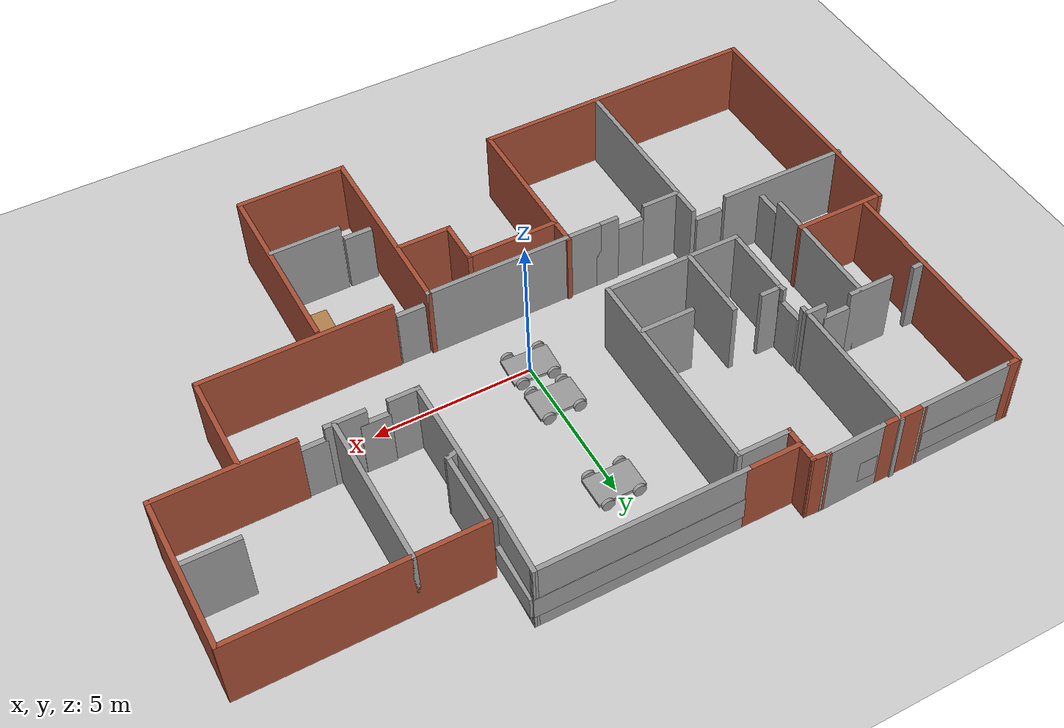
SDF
<sdf version="1.6">
 <world name="default">
  <plugin name="hello" filename="libhello.so"/>
  <light name="sun" type="directional">
   <pose>0 0 10 0 -0 0</pose>
   <diffuse>0.8 0.8 0.8 1</diffuse>
   <specular>0.2 0.2 0.2 1</specular>
   <attenuation>
    <range>1000</range>
    <constant>0.9</constant>
    <linear>0.01</linear>
    <quadratic>0.001</quadratic>
   </attenuation>
   <direction>-0.5 0.1 -0.9</direction>
  </light>
  <model name="ground_plane">
   <static>1</static>
   <link name="link">
    <collision name="collision">
     <geometry><plane><normal>0 0 1</normal><size>100 100</size></plane></geometry>
     <surface>
      <contact><collide_bitmask>65535</collide_bitmask></contact>
      <friction><ode><mu>100</mu><mu2>50</mu2></ode></friction>
     </surface>
    </collision>
    <visual name="visual">
     <cast_shadows>0</cast_shadows>
     <geometry><plane><normal>0 0 1</normal><size>100 100</size></plane></geometry>
     <material>
      <script><uri>file://media/materials/scripts/gazebo.material</uri><name>Gazebo/Grey</name></script>
     </material>
    </visual>
   </link>
  </model>
  <gravity>0 0 -9.8</gravity>
  <magnetic_field>6e-06 2.3e-05 -4.2e-05</magnetic_field>
  <atmosphere type="adiabatic"/>
  <physics name="default_physics" default="0" type="ode">
   <max_step_size>0.001</max_step_size>
   <real_time_factor>1</real_time_factor>
   <real_time_update_rate>1000</real_time_update_rate>
  </physics>
  <scene><ambient>0.4 0.4 0.4 1</ambient><background>0.7 0.7 0.7 1</background><shadows>1</shadows></scene>
  <spherical_coordinates>
   <surface_model>EARTH_WGS84</surface_model>
   <latitude_deg>0</latitude_deg>
   <longitude_deg>0</longitude_deg>
   <elevation>0</elevation>
   <heading_deg>0</heading_deg>
  </spherical_coordinates>
  <model name="rover">
   <link name="link_2">
    <inertial>
     <mass>1</mass>
     <inertia>
      <ixx>0.166667</ixx>
      <ixy>0</ixy>
      <ixz>0</ixz>
      <iyy>0.166667</iyy>
      <iyz>0</iyz>
      <izz>0.166667</izz>
     </inertia>
    </inertial>
    <visual name="visual">
     <geometry><box><size>1.5 1 0.1</size></box></geometry>
     <material>
      <lighting>1</lighting>
      <script><uri>file://media/materials/scripts/gazebo.material</uri><name>Gazebo/Grey</name></script>
      <shader type="pixel"><normal_map>__default__</normal_map></shader>
      <ambient>0.3 0.3 0.3 1</ambient>
      <diffuse>0.7 0.7 0.7 1</diffuse>
      <specular>0.01 0.01 0.01 1</specular>
      <emissive>0 0 0 1</emissive>
     </material>
    </visual>
    <collision name="collision">
     <geometry><box><size>1.5 1 0.1</size></box></geometry>
     <surface>
      <friction>
       <ode><mu>1</mu><mu2>1</mu2><fdir1>0 0 0</fdir1><slip1>0</slip1><slip2>0</slip2></ode>
       <torsional>
        <coefficient>1</coefficient>
        <patch_radius>0</patch_radius>
        <surface_radius>0</surface_radius>
        <use_patch_radius>1</use_patch_radius>
        <ode><slip>0</slip></ode>
       </torsional>
      </friction>
      <bounce><restitution_coefficient>0</restitution_coefficient><threshold>1e+06</threshold></bounce>
      <contact>
       <collide_without_contact>0</collide_without_contact>
       <collide_without_contact_bitmask>1</collide_without_contact_bitmask>
       <collide_bitmask>1</collide_bitmask>
       <ode>
        <soft_cfm>0</soft_cfm>
        <soft_erp>0.2</soft_erp>
        <kp>1e+13</kp>
        <kd>1</kd>
        <max_vel>0.01</max_vel>
        <min_depth>0</min_depth>
       </ode>
       <bullet>
        <split_impulse>1</split_impulse>
        <split_impulse_penetration_threshold>-0.01</split_impulse_penetration_threshold>
        <soft_cfm>0</soft_cfm>
        <soft_erp>0.2</soft_erp>
        <kp>1e+13</kp>
        <kd>1</kd>
       </bullet>
      </contact>
     </surface>
    </collision>
   </link>
   <link name="link_3">
    <pose>-0.5 -0.550019 0 1.5707 -0 0</pose>
    <inertial>
     <mass>1</mass>
     <inertia><ixx>0.145833</ixx><ixy>0</ixy><ixz>0</ixz><iyy>0.145833</iyy><iyz>0</iyz><izz>0.125</izz></inertia>
    </inertial>
    <visual name="visual">
     <geometry><cylinder><radius>0.2</radius><length>0.1</length></cylinder></geometry>
     <material>
      <lighting>1</lighting>
      <script><uri>file://media/materials/scripts/gazebo.material</uri><name>Gazebo/Grey</name></script>
      <shader type="pixel"><normal_map>__default__</normal_map></shader>
      <ambient>0.3 0.3 0.3 1</ambient>
      <diffuse>0.7 0.7 0.7 1</diffuse>
      <specular>0.01 0.01 0.01 1</specular>
      <emissive>0 0 0 1</emissive>
     </material>
    </visual>
    <collision name="collision">
     <geometry><cylinder><radius>0.2</radius><length>0.1</length></cylinder></geometry>
     <surface>
      <friction>
       <ode><mu>1</mu><mu2>1</mu2><fdir1>0 0 0</fdir1><slip1>0</slip1><slip2>0</slip2></ode>
       <torsional>
        <coefficient>1</coefficient>
        <patch_radius>0</patch_radius>
        <surface_radius>0</surface_radius>
        <use_patch_radius>1</use_patch_radius>
        <ode><slip>0</slip></ode>
       </torsional>
      </friction>
      <bounce><restitution_coefficient>0</restitution_coefficient><threshold>1e+06</threshold></bounce>
      <contact>
       <collide_without_contact>0</collide_without_contact>
       <collide_without_contact_bitmask>1</collide_without_contact_bitmask>
       <collide_bitmask>1</collide_bitmask>
       <ode>
        <soft_cfm>0</soft_cfm>
        <soft_erp>0.2</soft_erp>
        <kp>1e+13</kp>
        <kd>1</kd>
        <max_vel>0.01</max_vel>
        <min_depth>0</min_depth>
       </ode>
       <bullet>
        <split_impulse>1</split_impulse>
        <split_impulse_penetration_threshold>-0.01</split_impulse_penetration_threshold>
        <soft_cfm>0</soft_cfm>
        <soft_erp>0.2</soft_erp>
        <kp>1e+13</kp>
        <kd>1</kd>
       </bullet>
      </contact>
     </surface>
    </collision>
   </link>
   <link name="link_3_clone">
    <pose>-0.5 0.550019 0 1.5707 -0 0</pose>
    <inertial>
     <mass>1</mass>
     <inertia><ixx>0.145833</ixx><ixy>0</ixy><ixz>0</ixz><iyy>0.145833</iyy><iyz>0</iyz><izz>0.125</izz></inertia>
    </inertial>
    <visual name="visual">
     <geometry><cylinder><radius>0.2</radius><length>0.1</length></cylinder></geometry>
     <material>
      <lighting>1</lighting>
      <script><uri>file://media/materials/scripts/gazebo.material</uri><name>Gazebo/Grey</name></script>
      <shader type="pixel"><normal_map>__default__</normal_map></shader>
      <ambient>0.3 0.3 0.3 1</ambient>
      <diffuse>0.7 0.7 0.7 1</diffuse>
      <specular>0.01 0.01 0.01 1</specular>
      <emissive>0 0 0 1</emissive>
     </material>
    </visual>
    <collision name="collision">
     <geometry><cylinder><radius>0.2</radius><length>0.1</length></cylinder></geometry>
     <surface>
      <friction>
       <ode><mu>1</mu><mu2>1</mu2><fdir1>0 0 0</fdir1><slip1>0</slip1><slip2>0</slip2></ode>
       <torsional>
        <coefficient>1</coefficient>
        <patch_radius>0</patch_radius>
        <surface_radius>0</surface_radius>
        <use_patch_radius>1</use_patch_radius>
        <ode><slip>0</slip></ode>
       </torsional>
      </friction>
      <bounce><restitution_coefficient>0</restitution_coefficient><threshold>1e+06</threshold></bounce>
      <contact>
       <collide_without_contact>0</collide_without_contact>
       <collide_without_contact_bitmask>1</collide_without_contact_bitmask>
       <collide_bitmask>1</collide_bitmask>
       <ode>
        <soft_cfm>0</soft_cfm>
        <soft_erp>0.2</soft_erp>
        <kp>1e+13</kp>
        <kd>1</kd>
        <max_vel>0.01</max_vel>
        <min_depth>0</min_depth>
       </ode>
       <bullet>
        <split_impulse>1</split_impulse>
        <split_impulse_penetration_threshold>-0.01</split_impulse_penetration_threshold>
        <soft_cfm>0</soft_cfm>
        <soft_erp>0.2</soft_erp>
        <kp>1e+13</kp>
        <kd>1</kd>
       </bullet>
      </contact>
     </surface>
    </collision>
   </link>
   <link name="link_3_clone_0">
    <pose>0.5 -0.550019 0 1.5707 -0 0</pose>
    <inertial>
     <mass>1</mass>
     <inertia><ixx>0.145833</ixx><ixy>0</ixy><ixz>0</ixz><iyy>0.145833</iyy><iyz>0</iyz><izz>0.125</izz></inertia>
    </inertial>
    <visual name="visual">
     <geometry><cylinder><radius>0.2</radius><length>0.1</length></cylinder></geometry>
     <material>
      <lighting>1</lighting>
      <script><uri>file://media/materials/scripts/gazebo.material</uri><name>Gazebo/Grey</name></script>
      <shader type="pixel"><normal_map>__default__</normal_map></shader>
      <ambient>0.3 0.3 0.3 1</ambient>
      <diffuse>0.7 0.7 0.7 1</diffuse>
      <specular>0.01 0.01 0.01 1</specular>
      <emissive>0 0 0 1</emissive>
     </material>
    </visual>
    <collision name="collision">
     <geometry><cylinder><radius>0.2</radius><length>0.1</length></cylinder></geometry>
     <surface>
      <friction>
       <ode><mu>1</mu><mu2>1</mu2><fdir1>0 0 0</fdir1><slip1>0</slip1><slip2>0</slip2></ode>
       <torsional>
        <coefficient>1</coefficient>
        <patch_radius>0</patch_radius>
        <surface_radius>0</surface_radius>
        <use_patch_radius>1</use_patch_radius>
        <ode><slip>0</slip></ode>
       </torsional>
      </friction>
      <bounce><restitution_coefficient>0</restitution_coefficient><threshold>1e+06</threshold></bounce>
      <contact>
       <collide_without_contact>0</collide_without_contact>
       <collide_without_contact_bitmask>1</collide_without_contact_bitmask>
       <collide_bitmask>1</collide_bitmask>
       <ode>
        <soft_cfm>0</soft_cfm>
        <soft_erp>0.2</soft_erp>
        <kp>1e+13</kp>
        <kd>1</kd>
        <max_vel>0.01</max_vel>
        <min_depth>0</min_depth>
       </ode>
       <bullet>
        <split_impulse>1</split_impulse>
        <split_impulse_penetration_threshold>-0.01</split_impulse_penetration_threshold>
        <soft_cfm>0</soft_cfm>
        <soft_erp>0.2</soft_erp>
        <kp>1e+13</kp>
        <kd>1</kd>
       </bullet>
      </contact>
     </surface>
    </collision>
   </link>
   <link name="link_3_clone_clone">
    <pose>0.5 0.550019 0 1.5707 -0 0</pose>
    <inertial>
     <mass>1</mass>
     <inertia><ixx>0.145833</ixx><ixy>0</ixy><ixz>0</ixz><iyy>0.145833</iyy><iyz>0</iyz><izz>0.125</izz></inertia>
    </inertial>
    <visual name="visual">
     <geometry><cylinder><radius>0.2</radius><length>0.1</length></cylinder></geometry>
     <material>
      <lighting>1</lighting>
      <script><uri>file://media/materials/scripts/gazebo.material</uri><name>Gazebo/Grey</name></script>
      <shader type="pixel"><normal_map>__default__</normal_map></shader>
      <ambient>0.3 0.3 0.3 1</ambient>
      <diffuse>0.7 0.7 0.7 1</diffuse>
      <specular>0.01 0.01 0.01 1</specular>
      <emissive>0 0 0 1</emissive>
     </material>
    </visual>
    <collision name="collision">
     <geometry><cylinder><radius>0.2</radius><length>0.1</length></cylinder></geometry>
     <surface>
      <friction>
       <ode><mu>1</mu><mu2>1</mu2><fdir1>0 0 0</fdir1><slip1>0</slip1><slip2>0</slip2></ode>
       <torsional>
        <coefficient>1</coefficient>
        <patch_radius>0</patch_radius>
        <surface_radius>0</surface_radius>
        <use_patch_radius>1</use_patch_radius>
        <ode><slip>0</slip></ode>
       </torsional>
      </friction>
      <bounce><restitution_coefficient>0</restitution_coefficient><threshold>1e+06</threshold></bounce>
      <contact>
       <collide_without_contact>0</collide_without_contact>
       <collide_without_contact_bitmask>1</collide_without_contact_bitmask>
       <collide_bitmask>1</collide_bitmask>
       <ode>
        <soft_cfm>0</soft_cfm>
        <soft_erp>0.2</soft_erp>
        <kp>1e+13</kp>
        <kd>1</kd>
        <max_vel>0.01</max_vel>
        <min_depth>0</min_depth>
       </ode>
       <bullet>
        <split_impulse>1</split_impulse>
        <split_impulse_penetration_threshold>-0.01</split_impulse_penetration_threshold>
        <soft_cfm>0</soft_cfm>
        <soft_erp>0.2</soft_erp>
        <kp>1e+13</kp>
        <kd>1</kd>
       </bullet>
      </contact>
     </surface>
    </collision>
   </link>
   <joint name="link_2_JOINT_0" type="revolute">
    <parent>link_2</parent>
    <child>link_3</child>
    <axis>
     <xyz>0 0 1</xyz>
     <use_parent_model_frame>0</use_parent_model_frame>
     <limit>
      <lower>-1.79769e+308</lower>
      <upper>1.79769e+308</upper>
      <effort>-1</effort>
      <velocity>-1</velocity>
     </limit>
     <dynamics>
      <spring_reference>0</spring_reference>
      <spring_stiffness>0</spring_stiffness>
      <damping>0</damping>
     </dynamics>
    </axis>
    <physics>
     <ode><limit><cfm>0</cfm><erp>0.2</erp></limit><suspension><cfm>0</cfm><erp>0.2</erp></suspension></ode>
    </physics>
   </joint>
   <joint name="link_2_JOINT_1" type="revolute">
    <parent>link_2</parent>
    <child>link_3_clone</child>
    <axis>
     <xyz>1 0 0</xyz>
     <use_parent_model_frame>0</use_parent_model_frame>
     <limit>
      <lower>-1.79769e+308</lower>
      <upper>1.79769e+308</upper>
      <effort>-1</effort>
      <velocity>-1</velocity>
     </limit>
     <dynamics>
      <spring_reference>0</spring_reference>
      <spring_stiffness>0</spring_stiffness>
      <damping>0</damping>
     </dynamics>
    </axis>
    <physics>
     <ode><limit><cfm>0</cfm><erp>0.2</erp></limit><suspension><cfm>0</cfm><erp>0.2</erp></suspension></ode>
    </physics>
   </joint>
   <joint name="link_2_JOINT_2" type="revolute">
    <parent>link_2</parent>
    <child>link_3_clone_0</child>
    <axis>
     <xyz>1 0 0</xyz>
     <use_parent_model_frame>0</use_parent_model_frame>
     <limit>
      <lower>-1.79769e+308</lower>
      <upper>1.79769e+308</upper>
      <effort>-1</effort>
      <velocity>-1</velocity>
     </limit>
     <dynamics>
      <spring_reference>0</spring_reference>
      <spring_stiffness>0</spring_stiffness>
      <damping>0</damping>
     </dynamics>
    </axis>
    <physics>
     <ode><limit><cfm>0</cfm><erp>0.2</erp></limit><suspension><cfm>0</cfm><erp>0.2</erp></suspension></ode>
    </physics>
   </joint>
   <joint name="link_2_JOINT_3" type="revolute">
    <parent>link_2</parent>
    <child>link_3_clone_clone</child>
    <axis>
     <xyz>1 0 0</xyz>
     <use_parent_model_frame>0</use_parent_model_frame>
     <limit>
      <lower>-1.79769e+308</lower>
      <upper>1.79769e+308</upper>
      <effort>-1</effort>
      <velocity>-1</velocity>
     </limit>
     <dynamics>
      <spring_reference>0</spring_reference>
      <spring_stiffness>0</spring_stiffness>
      <damping>0</damping>
     </dynamics>
    </axis>
    <physics>
     <ode><limit><cfm>0</cfm><erp>0.2</erp></limit><suspension><cfm>0</cfm><erp>0.2</erp></suspension></ode>
    </physics>
   </joint>
   <static>0</static>
   <pose>-0.030591 -0.023282 0.200001 -3e-06 5e-06 -0.051996</pose>
  </model>
  <model name="myworld">
   <pose>-0.01124 0.05347 0 0 -0 0</pose>
   <link name="Door_0">
    <collision name="Door_0_Collision">
     <geometry><box><size>0.9 0.17 2</size></box></geometry>
     <pose>0 0 1 0 -0 0</pose>
    </collision>
    <visual name="Door_0_Visual">
     <pose>0 0 1 0 -0 0</pose>
     <geometry><box><size>0.9 0.17 2</size></box></geometry>
     <material>
      <script><uri>file://media/materials/scripts/gazebo.material</uri><name>Gazebo/Grey</name></script>
     </material>
    </visual>
    <pose>-6.89041 -1.3623 0 0 -0 0</pose>
   </link>
   <link name="Door_1">
    <collision name="Door_1_Collision">
     <geometry><box><size>0.9 0.17 2</size></box></geometry>
     <pose>0 0 1 0 -0 0</pose>
    </collision>
    <visual name="Door_1_Visual">
     <pose>0 0 1 0 -0 0</pose>
     <geometry><box><size>0.9 0.17 2</size></box></geometry>
     <material>
      <script><uri>file://media/materials/scripts/gazebo.material</uri><name>Gazebo/Grey</name></script>
     </material>
    </visual>
    <pose>-4.6028 -2.2135 0 0 -0 0</pose>
   </link>
   <link name="Door_3">
    <collision name="Door_3_Collision">
     <geometry><box><size>0.9 0.17 2</size></box></geometry>
     <pose>0 0 1 0 -0 0</pose>
    </collision>
    <visual name="Door_3_Visual">
     <pose>0 0 1 0 -0 0</pose>
     <geometry><box><size>0.9 0.17 2</size></box></geometry>
     <material>
      <script><uri>file://media/materials/scripts/gazebo.material</uri><name>Gazebo/Grey</name></script>
     </material>
    </visual>
    <pose>2.68566 -2.2401 0 0 -0 0</pose>
   </link>
   <link name="Door_4">
    <collision name="Door_4_Collision">
     <geometry><box><size>0.9 0.17 2</size></box></geometry>
     <pose>0 0 1 0 -0 0</pose>
    </collision>
    <visual name="Door_4_Visual">
     <pose>0 0 1 0 -0 0</pose>
     <geometry><box><size>0.9 0.17 2</size></box></geometry>
     <material>
      <script><uri>file://media/materials/scripts/gazebo.material</uri><name>Gazebo/Grey</name></script>
     </material>
    </visual>
    <pose>2.71226 -5.88433 0 0 -0 0</pose>
   </link>
   <link name="Door_5">
    <collision name="Door_5_Collision">
     <geometry><box><size>0.9 0.17 2</size></box></geometry>
     <pose>0 0 1 0 -0 0</pose>
    </collision>
    <visual name="Door_5_Visual">
     <pose>0 0 1 0 -0 0</pose>
     <geometry><box><size>0.9 0.17 2</size></box></geometry>
     <material>
      <script><uri>file://media/materials/scripts/gazebo.material</uri><name>Gazebo/Grey</name></script>
     </material>
    </visual>
    <pose>7.07469 0.898721 0 0 0 -3.14159</pose>
   </link>
   <link name="Door_6">
    <collision name="Door_6_Collision">
     <geometry><box><size>0.9 0.17 2</size></box></geometry>
     <pose>0 0 1 0 -0 0</pose>
    </collision>
    <visual name="Door_6_Visual">
     <pose>0 0 1 0 -0 0</pose>
     <geometry><box><size>0.9 0.17 2</size></box></geometry>
     <material>
      <script><uri>file://media/materials/scripts/gazebo.material</uri><name>Gazebo/Grey</name></script>
     </material>
    </visual>
    <pose>5.23928 0.925321 0 0 -0 3.11493</pose>
   </link>
   <link name="Door_7">
    <collision name="Door_7_Collision">
     <geometry><box><size>0.9 0.17 2</size></box></geometry>
     <pose>0 0 1 0 -0 0</pose>
    </collision>
    <visual name="Door_7_Visual">
     <pose>0 0 1 0 -0 0</pose>
     <geometry><box><size>0.9 0.17 2</size></box></geometry>
     <material>
      <script><uri>file://media/materials/scripts/gazebo.material</uri><name>Gazebo/Grey</name></script>
     </material>
    </visual>
    <pose>-8.75243 -0.803692 0 0 0 -1.56587</pose>
   </link>
   <link name="Door_8">
    <collision name="Door_8_Collision">
     <geometry><box><size>0.9 0.17 2</size></box></geometry>
     <pose>0 0 1 0 -0 0</pose>
    </collision>
    <visual name="Door_8_Visual">
     <pose>0 0 1 0 -0 0</pose>
     <geometry><box><size>0.9 0.17 2</size></box></geometry>
     <material>
      <script><uri>file://media/materials/scripts/gazebo.material</uri><name>Gazebo/Grey</name></script>
     </material>
    </visual>
    <pose>-6.82534 3.1576 0 0 -0 1.6011</pose>
   </link>
   <link name="Door_9">
    <collision name="Door_9_Collision">
     <geometry><box><size>0.9 0.17 2</size></box></geometry>
     <pose>0 0 1 0 -0 0</pose>
    </collision>
    <visual name="Door_9_Visual">
     <pose>0 0 1 0 -0 0</pose>
     <geometry><box><size>0.9 0.17 2</size></box></geometry>
     <material>
      <script><uri>file://media/materials/scripts/gazebo.material</uri><name>Gazebo/Grey</name></script>
     </material>
    </visual>
    <pose>-7.90122 3.88033 0 0 0 -3.13928</pose>
   </link>
   <link name="Wall_13">
    <collision name="Wall_13_Collision">
     <geometry><box><size>9.25 0.15 2.5</size></box></geometry>
     <pose>0 0 1.25 0 -0 0</pose>
    </collision>
    <visual name="Wall_13_Visual">
     <pose>0 0 1.25 0 -0 0</pose>
     <geometry><box><size>9.25 0.15 2.5</size></box></geometry>
     <material>
      <script><uri>file://media/materials/scripts/gazebo.material</uri><name>Gazebo/Bricks</name></script>
      <ambient>1 1 1 1</ambient>
     </material>
     <meta><layer>0</layer></meta>
    </visual>
    <pose>-6.98459 -7.19234 0 0 -0 0</pose>
   </link>
   <link name="Wall_14">
    <collision name="Wall_14_Collision">
     <geometry><box><size>5.25 0.15 2.5</size></box></geometry>
     <pose>0 0 1.25 0 -0 0</pose>
    </collision>
    <visual name="Wall_14_Visual">
     <pose>0 0 1.25 0 -0 0</pose>
     <geometry><box><size>5.25 0.15 2.5</size></box></geometry>
     <material>
      <script><uri>file://media/materials/scripts/gazebo.material</uri><name>Gazebo/Bricks</name></script>
      <ambient>1 1 1 1</ambient>
     </material>
     <meta><layer>0</layer></meta>
    </visual>
    <pose>-2.43459 -4.64234 0 0 -0 1.5708</pose>
   </link>
   <link name="Wall_16">
    <collision name="Wall_16_Collision">
     <geometry><box><size>3 0.15 2.5</size></box></geometry>
     <pose>0 0 1.25 0 -0 0</pose>
    </collision>
    <visual name="Wall_16_Visual">
     <pose>0 0 1.25 0 -0 0</pose>
     <geometry><box><size>3 0.15 2.5</size></box></geometry>
     <material>
      <script><uri>file://media/materials/scripts/gazebo.material</uri><name>Gazebo/Bricks</name></script>
      <ambient>1 1 1 1</ambient>
     </material>
     <meta><layer>0</layer></meta>
    </visual>
    <pose>-0.990907 -2.90731 0 0 -0 0</pose>
   </link>
   <link name="Wall_17">
    <collision name="Wall_17_Collision">
     <geometry><box><size>1.5 0.15 2.5</size></box></geometry>
     <pose>0 0 1.25 0 -0 0</pose>
    </collision>
    <visual name="Wall_17_Visual">
     <pose>0 0 1.25 0 -0 0</pose>
     <geometry><box><size>1.5 0.15 2.5</size></box></geometry>
     <material>
      <script><uri>file://media/materials/scripts/gazebo.material</uri><name>Gazebo/Bricks</name></script>
      <ambient>1 1 1 1</ambient>
     </material>
     <meta><layer>0</layer></meta>
    </visual>
    <pose>0.434093 -3.5823 0 0 0 -1.5708</pose>
   </link>
   <link name="Wall_18">
    <collision name="Wall_18_Collision">
     <geometry><box><size>1.75 0.15 2.5</size></box></geometry>
     <pose>0 0 1.25 0 -0 0</pose>
    </collision>
    <visual name="Wall_18_Visual">
     <pose>0 0 1.25 0 -0 0</pose>
     <geometry><box><size>1.75 0.15 2.5</size></box></geometry>
     <material>
      <script><uri>file://media/materials/scripts/gazebo.material</uri><name>Gazebo/Bricks</name></script>
      <ambient>1 1 1 1</ambient>
     </material>
     <meta><layer>0</layer></meta>
    </visual>
    <pose>1.23409 -4.2573 0 0 -0 0</pose>
   </link>
   <link name="Wall_2">
    <collision name="Wall_2_Collision">
     <geometry><box><size>0.5 0.15 2.5</size></box></geometry>
     <pose>0 0 1.25 0 -0 0</pose>
    </collision>
    <visual name="Wall_2_Visual">
     <pose>0 0 1.25 0 -0 0</pose>
     <geometry><box><size>0.5 0.15 2.5</size></box></geometry>
     <material>
      <script><uri>file://media/materials/scripts/gazebo.material</uri><name>Gazebo/Bricks</name></script>
      <ambient>1 1 1 1</ambient>
     </material>
     <meta><layer>0</layer></meta>
    </visual>
    <pose>-10.7791 8.16539 0 0 -0 3.14159</pose>
   </link>
   <link name="Wall_20">
    <collision name="Wall_20_Collision">
     <geometry><box><size>6 0.15 2.5</size></box></geometry>
     <pose>0 0 1.25 0 -0 0</pose>
    </collision>
    <visual name="Wall_20_Visual">
     <pose>0 0 1.25 0 -0 0</pose>
     <geometry><box><size>6 0.15 2.5</size></box></geometry>
     <material>
      <script><uri>file://media/materials/scripts/gazebo.material</uri><name>Gazebo/Grey</name></script>
      <ambient>1 1 1 1</ambient>
     </material>
     <meta><layer>0</layer></meta>
    </visual>
    <pose>-6.27739 -4.25049 0 0 0 -1.5708</pose>
   </link>
   <link name="Wall_24">
    <collision name="Wall_24_Collision">
     <geometry><box><size>1.25 0.15 2.5</size></box></geometry>
     <pose>0 0 1.25 0 -0 0</pose>
    </collision>
    <visual name="Wall_24_Visual">
     <pose>0 0 1.25 0 -0 0</pose>
     <geometry><box><size>1.25 0.15 2.5</size></box></geometry>
     <material>
      <script><uri>file://media/materials/scripts/gazebo.material</uri><name>Gazebo/Grey</name></script>
      <ambient>1 1 1 1</ambient>
     </material>
     <meta><layer>0</layer></meta>
    </visual>
    <pose>-5.68087 -2.20945 0 0 -0 0</pose>
   </link>
   <link name="Wall_26">
    <collision name="Wall_26_Collision">
     <geometry><box><size>5.75 0.15 2.5</size></box></geometry>
     <pose>0 0 1.25 0 -0 0</pose>
    </collision>
    <visual name="Wall_26_Visual">
     <pose>0 0 1.25 0 -0 0</pose>
     <geometry><box><size>5.75 0.15 2.5</size></box></geometry>
     <material>
      <script><uri>file://media/materials/scripts/gazebo.material</uri><name>Gazebo/Grey</name></script>
      <ambient>1 1 1 1</ambient>
     </material>
     <meta><layer>0</layer></meta>
    </visual>
    <pose>-0.685957 -2.16292 0 0 -0 0</pose>
   </link>
   <link name="Wall_27">
    <collision name="Wall_27_Collision">
     <geometry><box><size>6.25 0.15 2.5</size></box></geometry>
     <pose>0 0 1.25 0 -0 0</pose>
    </collision>
    <visual name="Wall_27_Visual">
     <pose>0 0 1.25 0 -0 0</pose>
     <geometry><box><size>6.25 0.15 2.5</size></box></geometry>
     <material>
      <script><uri>file://media/materials/scripts/gazebo.material</uri><name>Gazebo/Bricks</name></script>
      <ambient>1 1 1 1</ambient>
     </material>
     <meta><layer>0</layer></meta>
    </visual>
    <pose>2.11404 -5.21292 0 0 0 -1.5708</pose>
   </link>
   <link name="Wall_28">
    <collision name="Wall_28_Collision">
     <geometry><box><size>3.5 0.15 2.5</size></box></geometry>
     <pose>0 0 1.25 0 -0 0</pose>
    </collision>
    <visual name="Wall_28_Visual">
     <pose>0 0 1.25 0 -0 0</pose>
     <geometry><box><size>3.5 0.15 2.5</size></box></geometry>
     <material>
      <script><uri>file://media/materials/scripts/gazebo.material</uri><name>Gazebo/Bricks</name></script>
      <ambient>1 1 1 1</ambient>
     </material>
     <meta><layer>0</layer></meta>
    </visual>
    <pose>3.78904 -8.26292 0 0 -0 0</pose>
   </link>
   <link name="Wall_29">
    <collision name="Wall_29_Collision">
     <geometry><box><size>6 0.15 2.5</size></box></geometry>
     <pose>0 0 1.25 0 -0 0</pose>
    </collision>
    <visual name="Wall_29_Visual">
     <pose>0 0 1.25 0 -0 0</pose>
     <geometry><box><size>6 0.15 2.5</size></box></geometry>
     <material>
      <script><uri>file://media/materials/scripts/gazebo.material</uri><name>Gazebo/Bricks</name></script>
      <ambient>1 1 1 1</ambient>
     </material>
     <meta><layer>0</layer></meta>
    </visual>
    <pose>5.46404 -5.33792 0 0 -0 1.5708</pose>
   </link>
   <link name="Wall_3">
    <collision name="Wall_3_Collision">
     <geometry><box><size>7.25 0.15 2.5</size></box></geometry>
     <pose>0 0 1.25 0 -0 0</pose>
    </collision>
    <visual name="Wall_3_Visual">
     <pose>0 0 1.25 0 -0 0</pose>
     <geometry><box><size>7.25 0.15 2.5</size></box></geometry>
     <material>
      <script><uri>file://media/materials/scripts/gazebo.material</uri><name>Gazebo/Bricks</name></script>
      <ambient>1 1 1 1</ambient>
     </material>
     <meta><layer>0</layer></meta>
    </visual>
    <pose>-10.9541 4.61539 0 0 0 -1.5708</pose>
   </link>
   <link name="Wall_31">
    <collision name="Wall_31_Collision">
     <geometry><box><size>6 0.15 2.5</size></box></geometry>
     <pose>0 0 1.25 0 -0 0</pose>
    </collision>
    <visual name="Wall_31_Visual">
     <pose>0 0 1.25 0 -0 0</pose>
     <geometry><box><size>6 0.15 2.5</size></box></geometry>
     <material>
      <script><uri>file://media/materials/scripts/gazebo.material</uri><name>Gazebo/Bricks</name></script>
      <ambient>1 1 1 1</ambient>
     </material>
     <meta><layer>0</layer></meta>
    </visual>
    <pose>6.18501 -2.20945 0 0 -0 0</pose>
   </link>
   <link name="Wall_32">
    <collision name="Wall_32_Collision">
     <geometry><box><size>3.25 0.15 2.5</size></box></geometry>
     <pose>0 0 1.25 0 -0 0</pose>
    </collision>
    <visual name="Wall_32_Visual">
     <pose>0 0 1.25 0 -0 0</pose>
     <geometry><box><size>3.25 0.15 2.5</size></box></geometry>
     <material>
      <script><uri>file://media/materials/scripts/gazebo.material</uri><name>Gazebo/Bricks</name></script>
      <ambient>1 1 1 1</ambient>
     </material>
     <meta><layer>0</layer></meta>
    </visual>
    <pose>9.11001 -0.659446 0 0 -0 1.5708</pose>
   </link>
   <link name="Wall_34">
    <collision name="Wall_34_Collision">
     <geometry><box><size>4.25 0.15 2.5</size></box></geometry>
     <pose>0 0 1.25 0 -0 0</pose>
    </collision>
    <visual name="Wall_34_Visual">
     <pose>0 0 1.25 0 -0 0</pose>
     <geometry><box><size>4.25 0.15 2.5</size></box></geometry>
     <material>
      <script><uri>file://media/materials/scripts/gazebo.material</uri><name>Gazebo/Grey</name></script>
      <ambient>1 1 1 1</ambient>
     </material>
     <meta><layer>0</layer></meta>
    </visual>
    <pose>-9.53701 -1.32549 0 0 -0 3.14159</pose>
   </link>
   <link name="Wall_36">
    <collision name="Wall_36_Collision">
     <geometry><box><size>2.25 0.15 2.5</size></box></geometry>
     <pose>0 0 1.25 0 -0 0</pose>
    </collision>
    <visual name="Wall_36_Visual">
     <pose>0 0 1.25 0 -0 0</pose>
     <geometry><box><size>2.25 0.15 2.5</size></box></geometry>
     <material>
      <script><uri>file://media/materials/scripts/gazebo.material</uri><name>Gazebo/Grey</name></script>
      <ambient>1 1 1 1</ambient>
     </material>
     <meta><layer>0</layer></meta>
    </visual>
    <pose>4.35653 -5.88483 0 0 -0 0</pose>
   </link>
   <link name="Wall_38">
    <collision name="Wall_38_Collision">
     <geometry><box><size>7.5 0.15 2.5</size></box></geometry>
     <pose>0 0 1.25 0 -0 0</pose>
    </collision>
    <visual name="Wall_38_Visual">
     <pose>0 0 1.25 0 -0 0</pose>
     <geometry><box><size>7.5 0.15 2.5</size></box></geometry>
     <material>
      <script><uri>file://media/materials/scripts/gazebo.material</uri><name>Gazebo/Bricks</name></script>
      <ambient>1 1 1 1</ambient>
     </material>
     <meta><layer>0</layer></meta>
    </visual>
    <pose>7.91201 5.79267 0 0 -0 0</pose>
   </link>
   <link name="Wall_39">
    <collision name="Wall_39_Collision">
     <geometry><box><size>5 0.15 2.5</size></box></geometry>
     <pose>0 0 1.25 0 -0 0</pose>
    </collision>
    <visual name="Wall_39_Visual">
     <pose>0 0 1.25 0 -0 0</pose>
     <geometry><box><size>5 0.15 2.5</size></box></geometry>
     <material>
      <script><uri>file://media/materials/scripts/gazebo.material</uri><name>Gazebo/Bricks</name></script>
      <ambient>1 1 1 1</ambient>
     </material>
     <meta><layer>0</layer></meta>
    </visual>
    <pose>11.587 3.36767 0 0 0 -1.5708</pose>
   </link>
   <link name="Wall_40">
    <collision name="Wall_40_Collision">
     <geometry><box><size>4.25 0.15 2.5</size></box></geometry>
     <pose>0 0 1.25 0 -0 0</pose>
    </collision>
    <visual name="Wall_40_Visual">
     <pose>0 0 1.25 0 -0 0</pose>
     <geometry><box><size>4.25 0.15 2.5</size></box></geometry>
     <material>
      <script><uri>file://media/materials/scripts/gazebo.material</uri><name>Gazebo/Bricks</name></script>
      <ambient>1 1 1 1</ambient>
     </material>
     <meta><layer>0</layer></meta>
    </visual>
    <pose>9.53701 0.942667 0 0 -0 3.14159</pose>
   </link>
   <link name="Wall_42">
    <collision name="Wall_42_Collision">
     <geometry><box><size>1.75 0.15 2.5</size></box></geometry>
     <pose>0 0 1.25 0 -0 0</pose>
    </collision>
    <visual name="Wall_42_Visual">
     <pose>0 0 1.25 0 -0 0</pose>
     <geometry><box><size>1.75 0.15 2.5</size></box></geometry>
     <material>
      <script><uri>file://media/materials/scripts/gazebo.material</uri><name>Gazebo/Grey</name></script>
      <ambient>1 1 1 1</ambient>
     </material>
     <meta><layer>0</layer></meta>
    </visual>
    <pose>10.7129 3.1408 0 0 -0 0</pose>
   </link>
   <link name="Wall_44">
    <collision name="Wall_44_Collision">
     <geometry><box><size>5 0.15 2.5</size></box></geometry>
     <pose>0 0 1.25 0 -0 0</pose>
    </collision>
    <visual name="Wall_44_Visual">
     <pose>0 0 1.25 0 -0 0</pose>
     <geometry><box><size>5 0.15 2.5</size></box></geometry>
     <material>
      <script><uri>file://media/materials/scripts/gazebo.material</uri><name>Gazebo/Grey</name></script>
      <ambient>1 1 1 1</ambient>
     </material>
     <meta><layer>0</layer></meta>
    </visual>
    <pose>6.37711 3.36767 0 0 0 -1.5708</pose>
   </link>
   <link name="Wall_46">
    <collision name="Wall_46_Collision">
     <geometry><box><size>1.25 0.15 2.5</size></box></geometry>
     <pose>0 0 1.25 0 -0 0</pose>
    </collision>
    <visual name="Wall_46_Visual">
     <pose>0 0 1.25 0 -0 0</pose>
     <geometry><box><size>1.25 0.15 2.5</size></box></geometry>
     <material>
      <script><uri>file://media/materials/scripts/gazebo.material</uri><name>Gazebo/Grey</name></script>
      <ambient>1 1 1 1</ambient>
     </material>
     <meta><layer>0</layer></meta>
    </visual>
    <pose>6.05973 0.907656 0 0 -0 3.14159</pose>
   </link>
   <link name="Wall_48">
    <collision name="Wall_48_Collision">
     <geometry><box><size>1 0.15 2.5</size></box></geometry>
     <pose>0 0 1.25 0 -0 0</pose>
    </collision>
    <visual name="Wall_48_Visual">
     <pose>0 0 1.25 0 -0 0</pose>
     <geometry><box><size>1 0.15 2.5</size></box></geometry>
     <material>
      <script><uri>file://media/materials/scripts/gazebo.material</uri><name>Gazebo/Grey</name></script>
      <ambient>1 1 1 1</ambient>
     </material>
     <meta><layer>0</layer></meta>
    </visual>
    <pose>4.32378 0.907656 0 0 -0 3.14159</pose>
   </link>
   <link name="Wall_49">
    <collision name="Wall_49_Collision">
     <geometry><box><size>5 0.15 2.5</size></box></geometry>
     <pose>0 0 1.25 0 -0 0</pose>
    </collision>
    <visual name="Wall_49_Visual">
     <pose>0 0 1.25 0 -0 0</pose>
     <geometry><box><size>5 0.15 2.5</size></box></geometry>
     <material>
      <script><uri>file://media/materials/scripts/gazebo.material</uri><name>Gazebo/Grey</name></script>
      <ambient>1 1 1 1</ambient>
     </material>
     <meta><layer>0</layer></meta>
    </visual>
    <pose>3.89878 3.33266 0 0 -0 1.5708</pose>
   </link>
   <link name="Wall_51">
    <collision name="Wall_51_Collision">
     <geometry><box><size>2.5 0.15 2.5</size></box></geometry>
     <pose>0 0 1.25 0 -0 0</pose>
    </collision>
    <visual name="Wall_51_Visual">
     <pose>0 0 1.25 0 -0 0</pose>
     <geometry><box><size>2.5 0.15 2.5</size></box></geometry>
     <material>
      <script><uri>file://media/materials/scripts/gazebo.material</uri><name>Gazebo/Grey</name></script>
      <ambient>1 1 1 1</ambient>
     </material>
     <meta><layer>0</layer></meta>
    </visual>
    <pose>4.23701 4.61767 0 0 0 -1.5708</pose>
   </link>
   <link name="Wall_52">
    <collision name="Wall_52_Collision">
     <geometry><box><size>0.5 0.15 2.5</size></box></geometry>
     <pose>0 0 1.25 0 -0 0</pose>
    </collision>
    <visual name="Wall_52_Visual">
     <pose>0 0 1.25 0 -0 0</pose>
     <geometry><box><size>0.5 0.15 2.5</size></box></geometry>
     <material>
      <script><uri>file://media/materials/scripts/gazebo.material</uri><name>Gazebo/Grey</name></script>
      <ambient>1 1 1 1</ambient>
     </material>
     <meta><layer>0</layer></meta>
    </visual>
    <pose>4.06798 3.39737 0 0 0 -2.87979</pose>
   </link>
   <link name="Wall_54">
    <collision name="Wall_54_Collision">
     <geometry><box><size>1.5 0.15 2.5</size></box></geometry>
     <pose>0 0 1.25 0 -0 0</pose>
    </collision>
    <visual name="Wall_54_Visual">
     <pose>0 0 1.25 0 -0 0</pose>
     <geometry><box><size>1.5 0.15 2.5</size></box></geometry>
     <material>
      <script><uri>file://media/materials/scripts/gazebo.material</uri><name>Gazebo/Bricks</name></script>
      <ambient>1 1 1 1</ambient>
     </material>
     <meta><layer>0</layer></meta>
    </visual>
    <pose>-6.99811 8.21191 0 0 -0 0</pose>
   </link>
   <link name="Wall_56">
    <collision name="Wall_56_Collision">
     <geometry><box><size>4.75 0.15 2.5</size></box></geometry>
     <pose>0 0 1.25 0 -0 0</pose>
    </collision>
    <visual name="Wall_56_Visual">
     <pose>0 0 1.25 0 -0 0</pose>
     <geometry><box><size>4.75 0.15 2.5</size></box></geometry>
     <material>
      <script><uri>file://media/materials/scripts/gazebo.material</uri><name>Gazebo/Grey</name></script>
      <ambient>1 1 1 1</ambient>
     </material>
     <meta><layer>0</layer></meta>
    </visual>
    <pose>-6.8822 5.95843 0 0 0 -1.5708</pose>
   </link>
   <link name="Wall_58">
    <collision name="Wall_58_Collision">
     <geometry><box><size>0.75 0.15 2.5</size></box></geometry>
     <pose>0 0 1.25 0 -0 0</pose>
    </collision>
    <visual name="Wall_58_Visual">
     <pose>0 0 1.25 0 -0 0</pose>
     <geometry><box><size>0.75 0.15 2.5</size></box></geometry>
     <material>
      <script><uri>file://media/materials/scripts/gazebo.material</uri><name>Gazebo/Grey</name></script>
      <ambient>1 1 1 1</ambient>
     </material>
     <meta><layer>0</layer></meta>
    </visual>
    <pose>-6.48434 2.62904 0 0 -0 3.14159</pose>
   </link>
   <link name="Wall_59">
    <collision name="Wall_59_Collision">
     <geometry><box><size>0.25 0.15 2.5</size></box></geometry>
     <pose>0 0 1.25 0 -0 0</pose>
    </collision>
    <visual name="Wall_59_Visual">
     <pose>0 0 1.25 0 -0 0</pose>
     <geometry><box><size>0.25 0.15 2.5</size></box></geometry>
     <material>
      <script><uri>file://media/materials/scripts/gazebo.material</uri><name>Gazebo/Grey</name></script>
      <ambient>1 1 1 1</ambient>
     </material>
     <meta><layer>0</layer></meta>
    </visual>
    <pose>-6.79728 2.67734 0 0 -0 1.8326</pose>
   </link>
   <link name="Wall_6">
    <collision name="Wall_6_Collision">
     <geometry><box><size>3 0.15 2.5</size></box></geometry>
     <pose>0 0 1.25 0 -0 0</pose>
    </collision>
    <visual name="Wall_6_Visual">
     <pose>0 0 1.25 0 -0 0</pose>
     <geometry><box><size>3 0.15 2.5</size></box></geometry>
     <material>
      <script><uri>file://media/materials/scripts/gazebo.material</uri><name>Gazebo/Bricks</name></script>
      <ambient>1 1 1 1</ambient>
     </material>
     <meta><layer>0</layer></meta>
    </visual>
    <pose>-10.1096 0.907656 0 0 -0 0</pose>
   </link>
   <link name="Wall_62">
    <collision name="Wall_62_Collision">
     <geometry><box><size>2.5 0.15 2.5</size></box></geometry>
     <pose>0 0 1.25 0 -0 0</pose>
    </collision>
    <visual name="Wall_62_Visual">
     <pose>0 0 1.25 0 -0 0</pose>
     <geometry><box><size>2.5 0.15 2.5</size></box></geometry>
     <material>
      <script><uri>file://media/materials/scripts/gazebo.material</uri><name>Gazebo/Grey</name></script>
      <ambient>1 1 1 1</ambient>
     </material>
     <meta><layer>0</layer></meta>
    </visual>
    <pose>-6.78434 1.45404 0 0 0 -1.5708</pose>
   </link>
   <link name="Wall_63">
    <collision name="Wall_63_Collision">
     <geometry><box><size>4.5 0.15 2.5</size></box></geometry>
     <pose>0 0 1.25 0 -0 0</pose>
    </collision>
    <visual name="Wall_63_Visual">
     <pose>0 0 1.25 0 -0 0</pose>
     <geometry><box><size>4.5 0.15 2.5</size></box></geometry>
     <material>
      <script><uri>file://media/materials/scripts/gazebo.material</uri><name>Gazebo/Grey</name></script>
      <ambient>1 1 1 1</ambient>
     </material>
     <meta><layer>0</layer></meta>
    </visual>
    <pose>-4.60934 0.279041 0 0 -0 0</pose>
   </link>
   <link name="Wall_64">
    <collision name="Wall_64_Collision">
     <geometry><box><size>7 0.15 2.5</size></box></geometry>
     <pose>0 0 1.25 0 -0 0</pose>
    </collision>
    <visual name="Wall_64_Visual">
     <pose>0 0 1.25 0 -0 0</pose>
     <geometry><box><size>7 0.15 2.5</size></box></geometry>
     <material>
      <script><uri>file://media/materials/scripts/gazebo.material</uri><name>Gazebo/Grey</name></script>
      <ambient>1 1 1 1</ambient>
     </material>
     <meta><layer>0</layer></meta>
    </visual>
    <pose>-2.43434 3.70404 0 0 -0 1.5708</pose>
   </link>
   <link name="Wall_65">
    <collision name="Wall_65_Collision">
     <geometry><box><size>1.75 0.15 2.5</size></box></geometry>
     <pose>0 0 1.25 0 -0 0</pose>
    </collision>
    <visual name="Wall_65_Visual">
     <pose>0 0 1.25 0 -0 0</pose>
     <geometry><box><size>1.75 0.15 2.5</size></box></geometry>
     <material>
      <script><uri>file://media/materials/scripts/gazebo.material</uri><name>Gazebo/Grey</name></script>
      <ambient>1 1 1 1</ambient>
     </material>
     <meta><layer>0</layer></meta>
    </visual>
    <pose>-3.23434 7.12904 0 0 -0 3.14159</pose>
   </link>
   <link name="Wall_66">
    <collision name="Wall_66_Collision">
     <geometry><box><size>1.25 0.15 2.5</size></box></geometry>
     <pose>0 0 1.25 0 -0 0</pose>
    </collision>
    <visual name="Wall_66_Visual">
     <pose>0 0 1.25 0 -0 0</pose>
     <geometry><box><size>1.25 0.15 2.5</size></box></geometry>
     <material>
      <script><uri>file://media/materials/scripts/gazebo.material</uri><name>Gazebo/Bricks</name></script>
      <ambient>1 1 1 1</ambient>
     </material>
     <meta><layer>0</layer></meta>
    </visual>
    <pose>-4.03434 7.67904 0 0 -0 1.5708</pose>
   </link>
   <link name="Wall_69">
    <collision name="Wall_69_Collision">
     <geometry><box><size>0.626047 0.15 2.5</size></box></geometry>
     <pose>0 0 1.25 0 -0 0</pose>
    </collision>
    <visual name="Wall_69_Visual">
     <pose>0 0 1.25 0 -0 0</pose>
     <geometry><box><size>0.626047 0.15 2.5</size></box></geometry>
     <material>
      <script><uri>file://media/materials/scripts/gazebo.material</uri><name>Gazebo/Bricks</name></script>
      <ambient>1 1 1 1</ambient>
     </material>
     <meta><layer>0</layer></meta>
    </visual>
    <pose>-4.27191 8.24374 0 0 0 -0.061784</pose>
   </link>
   <link name="Wall_71">
    <collision name="Wall_71_Collision">
     <geometry><box><size>1.75 0.15 2.5</size></box></geometry>
     <pose>0 0 1.25 0 -0 0</pose>
    </collision>
    <visual name="Wall_71_Visual">
     <pose>0 0 1.25 0 -0 0</pose>
     <geometry><box><size>1.75 0.15 2.5</size></box></geometry>
     <material>
      <script><uri>file://media/materials/scripts/gazebo.material</uri><name>Gazebo/Bricks</name></script>
      <ambient>1 1 1 1</ambient>
     </material>
     <meta><layer>0</layer></meta>
    </visual>
    <pose>-3.19772 7.65362 0 0 -0 0</pose>
   </link>
   <link name="Wall_73">
    <collision name="Wall_73_Collision">
     <geometry><box><size>1.75 0.15 2.5</size></box></geometry>
     <pose>0 0 1.25 0 -0 0</pose>
    </collision>
    <visual name="Wall_73_Visual">
     <pose>0 0 1.25 0 -0 0</pose>
     <geometry><box><size>1.75 0.15 2.5</size></box></geometry>
     <material>
      <script><uri>file://media/materials/scripts/gazebo.material</uri><name>Gazebo/Grey</name></script>
      <ambient>1 1 1 1</ambient>
     </material>
     <meta><layer>0</layer></meta>
    </visual>
    <pose>-3.29077 2.11728 0 0 -0 0</pose>
   </link>
   <link name="Wall_75">
    <collision name="Wall_75_Collision">
     <geometry><box><size>2.5 0.15 2.5</size></box></geometry>
     <pose>0 0 1.25 0 -0 0</pose>
    </collision>
    <visual name="Wall_75_Visual">
     <pose>0 0 1.25 0 -0 0</pose>
     <geometry><box><size>2.5 0.15 2.5</size></box></geometry>
     <material>
      <script><uri>file://media/materials/scripts/gazebo.material</uri><name>Gazebo/Grey</name></script>
      <ambient>1 1 1 1</ambient>
     </material>
     <meta><layer>0</layer></meta>
    </visual>
    <pose>-5.16082 1.50056 0 0 0 -1.5708</pose>
   </link>
   <link name="Wall_8">
    <collision name="Wall_8_Collision">
     <geometry><box><size>8.25 0.15 2.5</size></box></geometry>
     <pose>0 0 1.25 0 -0 0</pose>
    </collision>
    <visual name="Wall_8_Visual">
     <pose>0 0 1.25 0 -0 0</pose>
     <geometry><box><size>8.25 0.15 2.5</size></box></geometry>
     <material>
      <script><uri>file://media/materials/scripts/gazebo.material</uri><name>Gazebo/Bricks</name></script>
      <ambient>1 1 1 1</ambient>
     </material>
     <meta><layer>0</layer></meta>
    </visual>
    <pose>-11.5346 -3.14234 0 0 0 -1.5708</pose>
   </link>
   <link name="Wall_82">
    <collision name="Wall_82_Collision">
     <geometry><box><size>0.5 0.15 2.5</size></box></geometry>
     <pose>0 0 1.25 0 -0 0</pose>
    </collision>
    <visual name="Wall_82_Visual">
     <pose>0 0 1.25 0 -0 0</pose>
     <geometry><box><size>0.5 0.15 2.5</size></box></geometry>
     <material>
      <script><uri>file://media/materials/scripts/gazebo.material</uri><name>Gazebo/Grey</name></script>
      <ambient>1 1 1 1</ambient>
     </material>
     <meta><layer>0</layer></meta>
    </visual>
    <pose>-10.7948 3.89702 0 0 -0 3.14159</pose>
   </link>
   <link name="Wall_84">
    <collision name="Wall_84_Collision">
     <geometry><box><size>1.5 0.15 2.5</size></box></geometry>
     <pose>0 0 1.25 0 -0 0</pose>
    </collision>
    <visual name="Wall_84_Visual">
     <pose>0 0 1.25 0 -0 0</pose>
     <geometry><box><size>1.5 0.15 2.5</size></box></geometry>
     <material>
      <script><uri>file://media/materials/scripts/gazebo.material</uri><name>Gazebo/Grey</name></script>
      <ambient>1 1 1 1</ambient>
     </material>
     <meta><layer>0</layer></meta>
    </visual>
    <pose>-9.0883 3.86643 0 0 -0 0</pose>
   </link>
   <link name="Wall_86">
    <collision name="Wall_86_Collision">
     <geometry><box><size>4.25 0.15 2.5</size></box></geometry>
     <pose>0 0 1.25 0 -0 0</pose>
    </collision>
    <visual name="Wall_86_Visual">
     <pose>0 0 1.25 0 -0 0</pose>
     <geometry><box><size>4.25 0.15 2.5</size></box></geometry>
     <material>
      <script><uri>file://media/materials/scripts/gazebo.material</uri><name>Gazebo/Grey</name></script>
      <ambient>1 1 1 1</ambient>
     </material>
     <meta><layer>0</layer></meta>
    </visual>
    <pose>-8.72323 1.81643 0 0 0 -1.5708</pose>
   </link>
   <link name="Wall_88">
    <collision name="Wall_88_Collision">
     <geometry><box><size>0.75 0.15 2.5</size></box></geometry>
     <pose>0 0 1.25 0 -0 0</pose>
    </collision>
    <visual name="Wall_88_Visual">
     <pose>0 0 1.25 0 -0 0</pose>
     <geometry><box><size>0.75 0.15 2.5</size></box></geometry>
     <material>
      <script><uri>file://media/materials/scripts/gazebo.material</uri><name>Gazebo/Grey</name></script>
      <ambient>1 1 1 1</ambient>
     </material>
     <meta><layer>0</layer></meta>
    </visual>
    <pose>-7.15805 3.8478 0 0 -0 0</pose>
   </link>
   <link name="Wall_90">
    <collision name="Wall_90_Collision">
     <geometry><box><size>0.75 0.15 2.5</size></box></geometry>
     <pose>0 0 1.25 0 -0 0</pose>
    </collision>
    <visual name="Wall_90_Visual">
     <pose>0 0 1.25 0 -0 0</pose>
     <geometry><box><size>0.75 0.15 2.5</size></box></geometry>
     <material>
      <script><uri>file://media/materials/scripts/gazebo.material</uri><name>Gazebo/Grey</name></script>
      <ambient>1 1 1 1</ambient>
     </material>
     <meta><layer>0</layer></meta>
    </visual>
    <pose>-3.78596 -2.16292 0 0 -0 3.14159</pose>
   </link>
   <link name="Wall_92">
    <collision name="Wall_92_Collision">
     <geometry><box><size>3.08138 0.15 2.5</size></box></geometry>
     <pose>0 0 1.25 0 -0 0</pose>
    </collision>
    <visual name="Wall_92_Visual">
     <pose>0 0 1.25 0 -0 0</pose>
     <geometry><box><size>3.08138 0.15 2.5</size></box></geometry>
     <material>
      <script><uri>file://media/materials/scripts/gazebo.material</uri><name>Gazebo/Grey</name></script>
      <ambient>1 1 1 1</ambient>
     </material>
     <meta><layer>0</layer></meta>
    </visual>
    <pose>-9.13861 8.18865 0 0 -0 0.015872</pose>
   </link>
   <link name="Wall_94">
    <collision name="Wall_94_Collision">
     <geometry><box><size>1.96422 0.15 2.5</size></box></geometry>
     <pose>0 0 1.25 0 -0 0</pose>
    </collision>
    <visual name="Wall_94_Visual">
     <pose>0 0 1.25 0 -0 0</pose>
     <geometry><box><size>1.96422 0.15 2.5</size></box></geometry>
     <material>
      <script><uri>file://media/materials/scripts/gazebo.material</uri><name>Gazebo/Grey</name></script>
      <ambient>1 1 1 1</ambient>
     </material>
     <meta><layer>0</layer></meta>
    </visual>
    <pose>-5.4163 8.23517 0 0 -0 0.025647</pose>
   </link>
   <link name="Wall_96">
    <collision name="Wall_96_Collision">
     <geometry><box><size>6.5 0.15 2.5</size></box></geometry>
     <pose>0 0 1.25 0 -0 0</pose>
    </collision>
    <visual name="Wall_96_Visual">
     <pose>0 0 1.25 0 -0 0</pose>
     <geometry><box><size>6.5 0.15 2.5</size></box></geometry>
     <material>
      <script><uri>file://media/materials/scripts/gazebo.material</uri><name>Gazebo/Grey</name></script>
      <ambient>1 1 1 1</ambient>
     </material>
     <meta><layer>0</layer></meta>
    </visual>
    <pose>0.77728 7.65362 0 0 -0 0</pose>
   </link>
   <link name="Wall_97">
    <collision name="Wall_97_Collision">
     <geometry><box><size>2.04672 0.15 2.5</size></box></geometry>
     <pose>0 0 1.25 0 -0 0</pose>
    </collision>
    <visual name="Wall_97_Visual">
     <pose>0 0 1.25 0 -0 0</pose>
     <geometry><box><size>2.04672 0.15 2.5</size></box></geometry>
     <material>
      <script><uri>file://media/materials/scripts/gazebo.material</uri><name>Gazebo/Grey</name></script>
      <ambient>1 1 1 1</ambient>
     </material>
     <meta><layer>0</layer></meta>
    </visual>
    <pose>3.92553 6.70564 0 0 0 -1.59901</pose>
   </link>
   <link name="Window_1">
    <collision name="Window_1_Collision">
     <geometry><box><size>2.75102 0.2 0.8</size></box></geometry>
     <pose>0 0 0.4 0 -0 0</pose>
    </collision>
    <visual name="Window_1_Visual">
     <pose>0 0 0.4 0 -0 0</pose>
     <geometry><box><size>2.75102 0.2 0.8</size></box></geometry>
     <material>
      <script><uri>file://media/materials/scripts/gazebo.material</uri><name>Gazebo/Grey</name></script>
     </material>
    </visual>
    <pose>-9.13968 8.19476 0.5 0 -0 0</pose>
   </link>
   <link name="Window_2">
    <collision name="Window_2_Collision">
     <geometry><box><size>1.73101 0.2 0.8</size></box></geometry>
     <pose>0 0 0.4 0 -0 0</pose>
    </collision>
    <visual name="Window_2_Visual">
     <pose>0 0 0.4 0 -0 0</pose>
     <geometry><box><size>1.73101 0.2 0.8</size></box></geometry>
     <material>
      <script><uri>file://media/materials/scripts/gazebo.material</uri><name>Gazebo/Grey</name></script>
     </material>
    </visual>
    <pose>-5.38532 8.20371 0.5 0 -0 0</pose>
   </link>
   <link name="Window_3">
    <collision name="Window_3_Collision">
     <geometry><box><size>6.39682 0.2 0.8</size></box></geometry>
     <pose>0 0 0.4 0 -0 0</pose>
    </collision>
    <visual name="Window_3_Visual">
     <pose>0 0 0.4 0 -0 0</pose>
     <geometry><box><size>6.39682 0.2 0.8</size></box></geometry>
     <material>
      <script><uri>file://media/materials/scripts/gazebo.material</uri><name>Gazebo/Grey</name></script>
     </material>
    </visual>
    <pose>0.847762 7.64984 0.5 0 -0 0</pose>
   </link>
   <link name="Window_4">
    <collision name="Window_4_Collision">
     <geometry><box><size>1.88438 0.2 0.8</size></box></geometry>
     <pose>0 0 0.4 0 -0 0</pose>
    </collision>
    <visual name="Window_4_Visual">
     <pose>0 0 0.4 0 -0 0</pose>
     <geometry><box><size>1.88438 0.2 0.8</size></box></geometry>
     <material>
      <script><uri>file://media/materials/scripts/gazebo.material</uri><name>Gazebo/Grey</name></script>
     </material>
    </visual>
    <pose>4.03095 6.75784 0.5 0 0 -1.5708</pose>
   </link>
   <static>1</static>
  </model>
  <model name="table">
   <static>1</static>
   <link name="link">
    <collision name="surface">
     <pose>0 0 1 0 -0 0</pose>
     <geometry><box><size>1.5 0.8 0.03</size></box></geometry>
     <surface><friction><ode><mu>0.6</mu><mu2>0.6</mu2></ode></friction></surface>
    </collision>
    <visual name="visual1">
     <pose>0 0 1 0 -0 0</pose>
     <geometry><box><size>1.5 0.8 0.03</size></box></geometry>
     <material>
      <script><uri>file://media/materials/scripts/gazebo.material</uri><name>Gazebo/Wood</name></script>
     </material>
    </visual>
    <collision name="front_left_leg">
     <pose>0.68 0.38 0.5 0 -0 0</pose>
     <geometry><cylinder><radius>0.02</radius><length>1</length></cylinder></geometry>
    </collision>
    <visual name="front_left_leg">
     <pose>0.68 0.38 0.5 0 -0 0</pose>
     <geometry><cylinder><radius>0.02</radius><length>1</length></cylinder></geometry>
     <material>
      <script><uri>file://media/materials/scripts/gazebo.material</uri><name>Gazebo/Grey</name></script>
     </material>
    </visual>
    <collision name="front_right_leg">
     <pose>0.68 -0.38 0.5 0 -0 0</pose>
     <geometry><cylinder><radius>0.02</radius><length>1</length></cylinder></geometry>
    </collision>
    <visual name="front_right_leg">
     <pose>0.68 -0.38 0.5 0 -0 0</pose>
     <geometry><cylinder><radius>0.02</radius><length>1</length></cylinder></geometry>
     <material>
      <script><uri>file://media/materials/scripts/gazebo.material</uri><name>Gazebo/Grey</name></script>
     </material>
    </visual>
    <collision name="back_right_leg">
     <pose>-0.68 -0.38 0.5 0 -0 0</pose>
     <geometry><cylinder><radius>0.02</radius><length>1</length></cylinder></geometry>
    </collision>
    <visual name="back_right_leg">
     <pose>-0.68 -0.38 0.5 0 -0 0</pose>
     <geometry><cylinder><radius>0.02</radius><length>1</length></cylinder></geometry>
     <material>
      <script><uri>file://media/materials/scripts/gazebo.material</uri><name>Gazebo/Grey</name></script>
     </material>
    </visual>
    <collision name="back_left_leg">
     <pose>-0.68 0.38 0.5 0 -0 0</pose>
     <geometry><cylinder><radius>0.02</radius><length>1</length></cylinder></geometry>
    </collision>
    <visual name="back_left_leg">
     <pose>-0.68 0.38 0.5 0 -0 0</pose>
     <geometry><cylinder><radius>0.02</radius><length>1</length></cylinder></geometry>
     <material>
      <script><uri>file://media/materials/scripts/gazebo.material</uri><name>Gazebo/Grey</name></script>
     </material>
    </visual>
   </link>
   <pose>4.92709 -3.57411 0 0 0 -1.59801</pose>
  </model>
  <model name="table_0">
   <static>1</static>
   <link name="link">
    <collision name="surface">
     <pose>0 0 1 0 -0 0</pose>
     <geometry><box><size>1.5 0.8 0.03</size></box></geometry>
     <surface><friction><ode><mu>0.6</mu><mu2>0.6</mu2></ode></friction></surface>
    </collision>
    <visual name="visual1">
     <pose>0 0 1 0 -0 0</pose>
     <geometry><box><size>1.5 0.8 0.03</size></box></geometry>
     <material>
      <script><uri>file://media/materials/scripts/gazebo.material</uri><name>Gazebo/Wood</name></script>
     </material>
    </visual>
    <collision name="front_left_leg">
     <pose>0.68 0.38 0.5 0 -0 0</pose>
     <geometry><cylinder><radius>0.02</radius><length>1</length></cylinder></geometry>
    </collision>
    <visual name="front_left_leg">
     <pose>0.68 0.38 0.5 0 -0 0</pose>
     <geometry><cylinder><radius>0.02</radius><length>1</length></cylinder></geometry>
     <material>
      <script><uri>file://media/materials/scripts/gazebo.material</uri><name>Gazebo/Grey</name></script>
     </material>
    </visual>
    <collision name="front_right_leg">
     <pose>0.68 -0.38 0.5 0 -0 0</pose>
     <geometry><cylinder><radius>0.02</radius><length>1</length></cylinder></geometry>
    </collision>
    <visual name="front_right_leg">
     <pose>0.68 -0.38 0.5 0 -0 0</pose>
     <geometry><cylinder><radius>0.02</radius><length>1</length></cylinder></geometry>
     <material>
      <script><uri>file://media/materials/scripts/gazebo.material</uri><name>Gazebo/Grey</name></script>
     </material>
    </visual>
    <collision name="back_right_leg">
     <pose>-0.68 -0.38 0.5 0 -0 0</pose>
     <geometry><cylinder><radius>0.02</radius><length>1</length></cylinder></geometry>
    </collision>
    <visual name="back_right_leg">
     <pose>-0.68 -0.38 0.5 0 -0 0</pose>
     <geometry><cylinder><radius>0.02</radius><length>1</length></cylinder></geometry>
     <material>
      <script><uri>file://media/materials/scripts/gazebo.material</uri><name>Gazebo/Grey</name></script>
     </material>
    </visual>
    <collision name="back_left_leg">
     <pose>-0.68 0.38 0.5 0 -0 0</pose>
     <geometry><cylinder><radius>0.02</radius><length>1</length></cylinder></geometry>
    </collision>
    <visual name="back_left_leg">
     <pose>-0.68 0.38 0.5 0 -0 0</pose>
     <geometry><cylinder><radius>0.02</radius><length>1</length></cylinder></geometry>
     <material>
      <script><uri>file://media/materials/scripts/gazebo.material</uri><name>Gazebo/Grey</name></script>
     </material>
    </visual>
   </link>
   <pose>-3.50642 6.71731 0 0 -0 0</pose>
  </model>
  <model name="rover_1">
   <link name="link_2">
    <inertial>
     <mass>1</mass>
     <inertia>
      <ixx>0.166667</ixx>
      <ixy>0</ixy>
      <ixz>0</ixz>
      <iyy>0.166667</iyy>
      <iyz>0</iyz>
      <izz>0.166667</izz>
     </inertia>
    </inertial>
    <visual name="visual">
     <geometry><box><size>1.5 1 0.1</size></box></geometry>
     <material>
      <lighting>1</lighting>
      <script><uri>file://media/materials/scripts/gazebo.material</uri><name>Gazebo/Grey</name></script>
      <shader type="pixel"><normal_map>__default__</normal_map></shader>
      <ambient>0.3 0.3 0.3 1</ambient>
      <diffuse>0.7 0.7 0.7 1</diffuse>
      <specular>0.01 0.01 0.01 1</specular>
      <emissive>0 0 0 1</emissive>
     </material>
    </visual>
    <collision name="collision">
     <geometry><box><size>1.5 1 0.1</size></box></geometry>
     <surface>
      <friction>
       <ode><mu>1</mu><mu2>1</mu2><fdir1>0 0 0</fdir1><slip1>0</slip1><slip2>0</slip2></ode>
       <torsional>
        <coefficient>1</coefficient>
        <patch_radius>0</patch_radius>
        <surface_radius>0</surface_radius>
        <use_patch_radius>1</use_patch_radius>
        <ode><slip>0</slip></ode>
       </torsional>
      </friction>
      <bounce><restitution_coefficient>0</restitution_coefficient><threshold>1e+06</threshold></bounce>
      <contact>
       <collide_without_contact>0</collide_without_contact>
       <collide_without_contact_bitmask>1</collide_without_contact_bitmask>
       <collide_bitmask>1</collide_bitmask>
       <ode>
        <soft_cfm>0</soft_cfm>
        <soft_erp>0.2</soft_erp>
        <kp>1e+13</kp>
        <kd>1</kd>
        <max_vel>0.01</max_vel>
        <min_depth>0</min_depth>
       </ode>
       <bullet>
        <split_impulse>1</split_impulse>
        <split_impulse_penetration_threshold>-0.01</split_impulse_penetration_threshold>
        <soft_cfm>0</soft_cfm>
        <soft_erp>0.2</soft_erp>
        <kp>1e+13</kp>
        <kd>1</kd>
       </bullet>
      </contact>
     </surface>
    </collision>
   </link>
   <link name="link_3">
    <pose>-0.5 -0.550019 -0 1.5707 -0 0</pose>
    <inertial>
     <mass>1</mass>
     <inertia><ixx>0.145833</ixx><ixy>0</ixy><ixz>0</ixz><iyy>0.145833</iyy><iyz>0</iyz><izz>0.125</izz></inertia>
    </inertial>
    <visual name="visual">
     <geometry><cylinder><radius>0.2</radius><length>0.1</length></cylinder></geometry>
     <material>
      <lighting>1</lighting>
      <script><uri>file://media/materials/scripts/gazebo.material</uri><name>Gazebo/Grey</name></script>
      <shader type="pixel"><normal_map>__default__</normal_map></shader>
      <ambient>0.3 0.3 0.3 1</ambient>
      <diffuse>0.7 0.7 0.7 1</diffuse>
      <specular>0.01 0.01 0.01 1</specular>
      <emissive>0 0 0 1</emissive>
     </material>
    </visual>
    <collision name="collision">
     <geometry><cylinder><radius>0.2</radius><length>0.1</length></cylinder></geometry>
     <surface>
      <friction>
       <ode><mu>1</mu><mu2>1</mu2><fdir1>0 0 0</fdir1><slip1>0</slip1><slip2>0</slip2></ode>
       <torsional>
        <coefficient>1</coefficient>
        <patch_radius>0</patch_radius>
        <surface_radius>0</surface_radius>
        <use_patch_radius>1</use_patch_radius>
        <ode><slip>0</slip></ode>
       </torsional>
      </friction>
      <bounce><restitution_coefficient>0</restitution_coefficient><threshold>1e+06</threshold></bounce>
      <contact>
       <collide_without_contact>0</collide_without_contact>
       <collide_without_contact_bitmask>1</collide_without_contact_bitmask>
       <collide_bitmask>1</collide_bitmask>
       <ode>
        <soft_cfm>0</soft_cfm>
        <soft_erp>0.2</soft_erp>
        <kp>1e+13</kp>
        <kd>1</kd>
        <max_vel>0.01</max_vel>
        <min_depth>0</min_depth>
       </ode>
       <bullet>
        <split_impulse>1</split_impulse>
        <split_impulse_penetration_threshold>-0.01</split_impulse_penetration_threshold>
        <soft_cfm>0</soft_cfm>
        <soft_erp>0.2</soft_erp>
        <kp>1e+13</kp>
        <kd>1</kd>
       </bullet>
      </contact>
     </surface>
    </collision>
   </link>
   <link name="link_3_clone">
    <pose>-0.5 0.550019 -0 1.5707 -0 0</pose>
    <inertial>
     <mass>1</mass>
     <inertia><ixx>0.145833</ixx><ixy>0</ixy><ixz>0</ixz><iyy>0.145833</iyy><iyz>0</iyz><izz>0.125</izz></inertia>
    </inertial>
    <visual name="visual">
     <geometry><cylinder><radius>0.2</radius><length>0.1</length></cylinder></geometry>
     <material>
      <lighting>1</lighting>
      <script><uri>file://media/materials/scripts/gazebo.material</uri><name>Gazebo/Grey</name></script>
      <shader type="pixel"><normal_map>__default__</normal_map></shader>
      <ambient>0.3 0.3 0.3 1</ambient>
      <diffuse>0.7 0.7 0.7 1</diffuse>
      <specular>0.01 0.01 0.01 1</specular>
      <emissive>0 0 0 1</emissive>
     </material>
    </visual>
    <collision name="collision">
     <geometry><cylinder><radius>0.2</radius><length>0.1</length></cylinder></geometry>
     <surface>
      <friction>
       <ode><mu>1</mu><mu2>1</mu2><fdir1>0 0 0</fdir1><slip1>0</slip1><slip2>0</slip2></ode>
       <torsional>
        <coefficient>1</coefficient>
        <patch_radius>0</patch_radius>
        <surface_radius>0</surface_radius>
        <use_patch_radius>1</use_patch_radius>
        <ode><slip>0</slip></ode>
       </torsional>
      </friction>
      <bounce><restitution_coefficient>0</restitution_coefficient><threshold>1e+06</threshold></bounce>
      <contact>
       <collide_without_contact>0</collide_without_contact>
       <collide_without_contact_bitmask>1</collide_without_contact_bitmask>
       <collide_bitmask>1</collide_bitmask>
       <ode>
        <soft_cfm>0</soft_cfm>
        <soft_erp>0.2</soft_erp>
        <kp>1e+13</kp>
        <kd>1</kd>
        <max_vel>0.01</max_vel>
        <min_depth>0</min_depth>
       </ode>
       <bullet>
        <split_impulse>1</split_impulse>
        <split_impulse_penetration_threshold>-0.01</split_impulse_penetration_threshold>
        <soft_cfm>0</soft_cfm>
        <soft_erp>0.2</soft_erp>
        <kp>1e+13</kp>
        <kd>1</kd>
       </bullet>
      </contact>
     </surface>
    </collision>
   </link>
   <link name="link_3_clone_0">
    <pose>0.5 -0.550019 0 1.5707 -0 0</pose>
    <inertial>
     <mass>1</mass>
     <inertia><ixx>0.145833</ixx><ixy>0</ixy><ixz>0</ixz><iyy>0.145833</iyy><iyz>0</iyz><izz>0.125</izz></inertia>
    </inertial>
    <visual name="visual">
     <geometry><cylinder><radius>0.2</radius><length>0.1</length></cylinder></geometry>
     <material>
      <lighting>1</lighting>
      <script><uri>file://media/materials/scripts/gazebo.material</uri><name>Gazebo/Grey</name></script>
      <shader type="pixel"><normal_map>__default__</normal_map></shader>
      <ambient>0.3 0.3 0.3 1</ambient>
      <diffuse>0.7 0.7 0.7 1</diffuse>
      <specular>0.01 0.01 0.01 1</specular>
      <emissive>0 0 0 1</emissive>
     </material>
    </visual>
    <collision name="collision">
     <geometry><cylinder><radius>0.2</radius><length>0.1</length></cylinder></geometry>
     <surface>
      <friction>
       <ode><mu>1</mu><mu2>1</mu2><fdir1>0 0 0</fdir1><slip1>0</slip1><slip2>0</slip2></ode>
       <torsional>
        <coefficient>1</coefficient>
        <patch_radius>0</patch_radius>
        <surface_radius>0</surface_radius>
        <use_patch_radius>1</use_patch_radius>
        <ode><slip>0</slip></ode>
       </torsional>
      </friction>
      <bounce><restitution_coefficient>0</restitution_coefficient><threshold>1e+06</threshold></bounce>
      <contact>
       <collide_without_contact>0</collide_without_contact>
       <collide_without_contact_bitmask>1</collide_without_contact_bitmask>
       <collide_bitmask>1</collide_bitmask>
       <ode>
        <soft_cfm>0</soft_cfm>
        <soft_erp>0.2</soft_erp>
        <kp>1e+13</kp>
        <kd>1</kd>
        <max_vel>0.01</max_vel>
        <min_depth>0</min_depth>
       </ode>
       <bullet>
        <split_impulse>1</split_impulse>
        <split_impulse_penetration_threshold>-0.01</split_impulse_penetration_threshold>
        <soft_cfm>0</soft_cfm>
        <soft_erp>0.2</soft_erp>
        <kp>1e+13</kp>
        <kd>1</kd>
       </bullet>
      </contact>
     </surface>
    </collision>
   </link>
   <link name="link_3_clone_clone">
    <pose>0.5 0.550019 0 1.5707 -0 0</pose>
    <inertial>
     <mass>1</mass>
     <inertia><ixx>0.145833</ixx><ixy>0</ixy><ixz>0</ixz><iyy>0.145833</iyy><iyz>0</iyz><izz>0.125</izz></inertia>
    </inertial>
    <visual name="visual">
     <geometry><cylinder><radius>0.2</radius><length>0.1</length></cylinder></geometry>
     <material>
      <lighting>1</lighting>
      <script><uri>file://media/materials/scripts/gazebo.material</uri><name>Gazebo/Grey</name></script>
      <shader type="pixel"><normal_map>__default__</normal_map></shader>
      <ambient>0.3 0.3 0.3 1</ambient>
      <diffuse>0.7 0.7 0.7 1</diffuse>
      <specular>0.01 0.01 0.01 1</specular>
      <emissive>0 0 0 1</emissive>
     </material>
    </visual>
    <collision name="collision">
     <geometry><cylinder><radius>0.2</radius><length>0.1</length></cylinder></geometry>
     <surface>
      <friction>
       <ode><mu>1</mu><mu2>1</mu2><fdir1>0 0 0</fdir1><slip1>0</slip1><slip2>0</slip2></ode>
       <torsional>
        <coefficient>1</coefficient>
        <patch_radius>0</patch_radius>
        <surface_radius>0</surface_radius>
        <use_patch_radius>1</use_patch_radius>
        <ode><slip>0</slip></ode>
       </torsional>
      </friction>
      <bounce><restitution_coefficient>0</restitution_coefficient><threshold>1e+06</threshold></bounce>
      <contact>
       <collide_without_contact>0</collide_without_contact>
       <collide_without_contact_bitmask>1</collide_without_contact_bitmask>
       <collide_bitmask>1</collide_bitmask>
       <ode>
        <soft_cfm>0</soft_cfm>
        <soft_erp>0.2</soft_erp>
        <kp>1e+13</kp>
        <kd>1</kd>
        <max_vel>0.01</max_vel>
        <min_depth>0</min_depth>
       </ode>
       <bullet>
        <split_impulse>1</split_impulse>
        <split_impulse_penetration_threshold>-0.01</split_impulse_penetration_threshold>
        <soft_cfm>0</soft_cfm>
        <soft_erp>0.2</soft_erp>
        <kp>1e+13</kp>
        <kd>1</kd>
       </bullet>
      </contact>
     </surface>
    </collision>
   </link>
   <joint name="link_2_JOINT_0" type="revolute">
    <parent>link_2</parent>
    <child>link_3</child>
    <axis>
     <xyz>0 0 1</xyz>
     <use_parent_model_frame>0</use_parent_model_frame>
     <limit>
      <lower>-1.79769e+308</lower>
      <upper>1.79769e+308</upper>
      <effort>-1</effort>
      <velocity>-1</velocity>
     </limit>
     <dynamics>
      <spring_reference>0</spring_reference>
      <spring_stiffness>0</spring_stiffness>
      <damping>0</damping>
      <friction>0</friction>
     </dynamics>
    </axis>
    <physics>
     <ode><limit><cfm>0</cfm><erp>0.2</erp></limit><suspension><cfm>0</cfm><erp>0.2</erp></suspension></ode>
    </physics>
   </joint>
   <joint name="link_2_JOINT_1" type="revolute">
    <parent>link_2</parent>
    <child>link_3_clone</child>
    <axis>
     <xyz>1 0 0</xyz>
     <use_parent_model_frame>0</use_parent_model_frame>
     <limit>
      <lower>-1.79769e+308</lower>
      <upper>1.79769e+308</upper>
      <effort>-1</effort>
      <velocity>-1</velocity>
     </limit>
     <dynamics>
      <spring_reference>0</spring_reference>
      <spring_stiffness>0</spring_stiffness>
      <damping>0</damping>
      <friction>0</friction>
     </dynamics>
    </axis>
    <physics>
     <ode><limit><cfm>0</cfm><erp>0.2</erp></limit><suspension><cfm>0</cfm><erp>0.2</erp></suspension></ode>
    </physics>
   </joint>
   <joint name="link_2_JOINT_2" type="revolute">
    <parent>link_2</parent>
    <child>link_3_clone_0</child>
    <axis>
     <xyz>1 0 0</xyz>
     <use_parent_model_frame>0</use_parent_model_frame>
     <limit>
      <lower>-1.79769e+308</lower>
      <upper>1.79769e+308</upper>
      <effort>-1</effort>
      <velocity>-1</velocity>
     </limit>
     <dynamics>
      <spring_reference>0</spring_reference>
      <spring_stiffness>0</spring_stiffness>
      <damping>0</damping>
      <friction>0</friction>
     </dynamics>
    </axis>
    <physics>
     <ode><limit><cfm>0</cfm><erp>0.2</erp></limit><suspension><cfm>0</cfm><erp>0.2</erp></suspension></ode>
    </physics>
   </joint>
   <joint name="link_2_JOINT_3" type="revolute">
    <parent>link_2</parent>
    <child>link_3_clone_clone</child>
    <axis>
     <xyz>1 0 0</xyz>
     <use_parent_model_frame>0</use_parent_model_frame>
     <limit>
      <lower>-1.79769e+308</lower>
      <upper>1.79769e+308</upper>
      <effort>-1</effort>
      <velocity>-1</velocity>
     </limit>
     <dynamics>
      <spring_reference>0</spring_reference>
      <spring_stiffness>0</spring_stiffness>
      <damping>0</damping>
      <friction>0</friction>
     </dynamics>
    </axis>
    <physics>
     <ode><limit><cfm>0</cfm><erp>0.2</erp></limit><suspension><cfm>0</cfm><erp>0.2</erp></suspension></ode>
    </physics>
   </joint>
   <static>0</static>
   <pose>-0.006865 4.89875 0.200001 -0 2e-06 -0.000764</pose>
  </model>
  <model name="rover_0">
   <link name="link_2">
    <inertial>
     <mass>1</mass>
     <inertia>
      <ixx>0.166667</ixx>
      <ixy>0</ixy>
      <ixz>0</ixz>
      <iyy>0.166667</iyy>
      <iyz>0</iyz>
      <izz>0.166667</izz>
     </inertia>
    </inertial>
    <visual name="visual">
     <geometry><box><size>1.5 1 0.1</size></box></geometry>
     <material>
      <lighting>1</lighting>
      <script><uri>file://media/materials/scripts/gazebo.material</uri><name>Gazebo/Grey</name></script>
      <shader type="pixel"><normal_map>__default__</normal_map></shader>
      <ambient>0.3 0.3 0.3 1</ambient>
      <diffuse>0.7 0.7 0.7 1</diffuse>
      <specular>0.01 0.01 0.01 1</specular>
      <emissive>0 0 0 1</emissive>
     </material>
    </visual>
    <collision name="collision">
     <geometry><box><size>1.5 1 0.1</size></box></geometry>
     <surface>
      <friction>
       <ode><mu>1</mu><mu2>1</mu2><fdir1>0 0 0</fdir1><slip1>0</slip1><slip2>0</slip2></ode>
       <torsional>
        <coefficient>1</coefficient>
        <patch_radius>0</patch_radius>
        <surface_radius>0</surface_radius>
        <use_patch_radius>1</use_patch_radius>
        <ode><slip>0</slip></ode>
       </torsional>
      </friction>
      <bounce><restitution_coefficient>0</restitution_coefficient><threshold>1e+06</threshold></bounce>
      <contact>
       <collide_without_contact>0</collide_without_contact>
       <collide_without_contact_bitmask>1</collide_without_contact_bitmask>
       <collide_bitmask>1</collide_bitmask>
       <ode>
        <soft_cfm>0</soft_cfm>
        <soft_erp>0.2</soft_erp>
        <kp>1e+13</kp>
        <kd>1</kd>
        <max_vel>0.01</max_vel>
        <min_depth>0</min_depth>
       </ode>
       <bullet>
        <split_impulse>1</split_impulse>
        <split_impulse_penetration_threshold>-0.01</split_impulse_penetration_threshold>
        <soft_cfm>0</soft_cfm>
        <soft_erp>0.2</soft_erp>
        <kp>1e+13</kp>
        <kd>1</kd>
       </bullet>
      </contact>
     </surface>
    </collision>
   </link>
   <link name="link_3">
    <pose>-0.5 -0.550019 -0 1.5707 -0 0</pose>
    <inertial>
     <mass>1</mass>
     <inertia><ixx>0.145833</ixx><ixy>0</ixy><ixz>0</ixz><iyy>0.145833</iyy><iyz>0</iyz><izz>0.125</izz></inertia>
    </inertial>
    <visual name="visual">
     <geometry><cylinder><radius>0.2</radius><length>0.1</length></cylinder></geometry>
     <material>
      <lighting>1</lighting>
      <script><uri>file://media/materials/scripts/gazebo.material</uri><name>Gazebo/Grey</name></script>
      <shader type="pixel"><normal_map>__default__</normal_map></shader>
      <ambient>0.3 0.3 0.3 1</ambient>
      <diffuse>0.7 0.7 0.7 1</diffuse>
      <specular>0.01 0.01 0.01 1</specular>
      <emissive>0 0 0 1</emissive>
     </material>
    </visual>
    <collision name="collision">
     <geometry><cylinder><radius>0.2</radius><length>0.1</length></cylinder></geometry>
     <surface>
      <friction>
       <ode><mu>1</mu><mu2>1</mu2><fdir1>0 0 0</fdir1><slip1>0</slip1><slip2>0</slip2></ode>
       <torsional>
        <coefficient>1</coefficient>
        <patch_radius>0</patch_radius>
        <surface_radius>0</surface_radius>
        <use_patch_radius>1</use_patch_radius>
        <ode><slip>0</slip></ode>
       </torsional>
      </friction>
      <bounce><restitution_coefficient>0</restitution_coefficient><threshold>1e+06</threshold></bounce>
      <contact>
       <collide_without_contact>0</collide_without_contact>
       <collide_without_contact_bitmask>1</collide_without_contact_bitmask>
       <collide_bitmask>1</collide_bitmask>
       <ode>
        <soft_cfm>0</soft_cfm>
        <soft_erp>0.2</soft_erp>
        <kp>1e+13</kp>
        <kd>1</kd>
        <max_vel>0.01</max_vel>
        <min_depth>0</min_depth>
       </ode>
       <bullet>
        <split_impulse>1</split_impulse>
        <split_impulse_penetration_threshold>-0.01</split_impulse_penetration_threshold>
        <soft_cfm>0</soft_cfm>
        <soft_erp>0.2</soft_erp>
        <kp>1e+13</kp>
        <kd>1</kd>
       </bullet>
      </contact>
     </surface>
    </collision>
   </link>
   <link name="link_3_clone">
    <pose>-0.5 0.550019 -0 1.5707 -0 0</pose>
    <inertial>
     <mass>1</mass>
     <inertia><ixx>0.145833</ixx><ixy>0</ixy><ixz>0</ixz><iyy>0.145833</iyy><iyz>0</iyz><izz>0.125</izz></inertia>
    </inertial>
    <visual name="visual">
     <geometry><cylinder><radius>0.2</radius><length>0.1</length></cylinder></geometry>
     <material>
      <lighting>1</lighting>
      <script><uri>file://media/materials/scripts/gazebo.material</uri><name>Gazebo/Grey</name></script>
      <shader type="pixel"><normal_map>__default__</normal_map></shader>
      <ambient>0.3 0.3 0.3 1</ambient>
      <diffuse>0.7 0.7 0.7 1</diffuse>
      <specular>0.01 0.01 0.01 1</specular>
      <emissive>0 0 0 1</emissive>
     </material>
    </visual>
    <collision name="collision">
     <geometry><cylinder><radius>0.2</radius><length>0.1</length></cylinder></geometry>
     <surface>
      <friction>
       <ode><mu>1</mu><mu2>1</mu2><fdir1>0 0 0</fdir1><slip1>0</slip1><slip2>0</slip2></ode>
       <torsional>
        <coefficient>1</coefficient>
        <patch_radius>0</patch_radius>
        <surface_radius>0</surface_radius>
        <use_patch_radius>1</use_patch_radius>
        <ode><slip>0</slip></ode>
       </torsional>
      </friction>
      <bounce><restitution_coefficient>0</restitution_coefficient><threshold>1e+06</threshold></bounce>
      <contact>
       <collide_without_contact>0</collide_without_contact>
       <collide_without_contact_bitmask>1</collide_without_contact_bitmask>
       <collide_bitmask>1</collide_bitmask>
       <ode>
        <soft_cfm>0</soft_cfm>
        <soft_erp>0.2</soft_erp>
        <kp>1e+13</kp>
        <kd>1</kd>
        <max_vel>0.01</max_vel>
        <min_depth>0</min_depth>
       </ode>
       <bullet>
        <split_impulse>1</split_impulse>
        <split_impulse_penetration_threshold>-0.01</split_impulse_penetration_threshold>
        <soft_cfm>0</soft_cfm>
        <soft_erp>0.2</soft_erp>
        <kp>1e+13</kp>
        <kd>1</kd>
       </bullet>
      </contact>
     </surface>
    </collision>
   </link>
   <link name="link_3_clone_0">
    <pose>0.5 -0.550019 0 1.5707 -0 0</pose>
    <inertial>
     <mass>1</mass>
     <inertia><ixx>0.145833</ixx><ixy>0</ixy><ixz>0</ixz><iyy>0.145833</iyy><iyz>0</iyz><izz>0.125</izz></inertia>
    </inertial>
    <visual name="visual">
     <geometry><cylinder><radius>0.2</radius><length>0.1</length></cylinder></geometry>
     <material>
      <lighting>1</lighting>
      <script><uri>file://media/materials/scripts/gazebo.material</uri><name>Gazebo/Grey</name></script>
      <shader type="pixel"><normal_map>__default__</normal_map></shader>
      <ambient>0.3 0.3 0.3 1</ambient>
      <diffuse>0.7 0.7 0.7 1</diffuse>
      <specular>0.01 0.01 0.01 1</specular>
      <emissive>0 0 0 1</emissive>
     </material>
    </visual>
    <collision name="collision">
     <geometry><cylinder><radius>0.2</radius><length>0.1</length></cylinder></geometry>
     <surface>
      <friction>
       <ode><mu>1</mu><mu2>1</mu2><fdir1>0 0 0</fdir1><slip1>0</slip1><slip2>0</slip2></ode>
       <torsional>
        <coefficient>1</coefficient>
        <patch_radius>0</patch_radius>
        <surface_radius>0</surface_radius>
        <use_patch_radius>1</use_patch_radius>
        <ode><slip>0</slip></ode>
       </torsional>
      </friction>
      <bounce><restitution_coefficient>0</restitution_coefficient><threshold>1e+06</threshold></bounce>
      <contact>
       <collide_without_contact>0</collide_without_contact>
       <collide_without_contact_bitmask>1</collide_without_contact_bitmask>
       <collide_bitmask>1</collide_bitmask>
       <ode>
        <soft_cfm>0</soft_cfm>
        <soft_erp>0.2</soft_erp>
        <kp>1e+13</kp>
        <kd>1</kd>
        <max_vel>0.01</max_vel>
        <min_depth>0</min_depth>
       </ode>
       <bullet>
        <split_impulse>1</split_impulse>
        <split_impulse_penetration_threshold>-0.01</split_impulse_penetration_threshold>
        <soft_cfm>0</soft_cfm>
        <soft_erp>0.2</soft_erp>
        <kp>1e+13</kp>
        <kd>1</kd>
       </bullet>
      </contact>
     </surface>
    </collision>
   </link>
   <link name="link_3_clone_clone">
    <pose>0.5 0.550019 0 1.5707 -0 0</pose>
    <inertial>
     <mass>1</mass>
     <inertia><ixx>0.145833</ixx><ixy>0</ixy><ixz>0</ixz><iyy>0.145833</iyy><iyz>0</iyz><izz>0.125</izz></inertia>
    </inertial>
    <visual name="visual">
     <geometry><cylinder><radius>0.2</radius><length>0.1</length></cylinder></geometry>
     <material>
      <lighting>1</lighting>
      <script><uri>file://media/materials/scripts/gazebo.material</uri><name>Gazebo/Grey</name></script>
      <shader type="pixel"><normal_map>__default__</normal_map></shader>
      <ambient>0.3 0.3 0.3 1</ambient>
      <diffuse>0.7 0.7 0.7 1</diffuse>
      <specular>0.01 0.01 0.01 1</specular>
      <emissive>0 0 0 1</emissive>
     </material>
    </visual>
    <collision name="collision">
     <geometry><cylinder><radius>0.2</radius><length>0.1</length></cylinder></geometry>
     <surface>
      <friction>
       <ode><mu>1</mu><mu2>1</mu2><fdir1>0 0 0</fdir1><slip1>0</slip1><slip2>0</slip2></ode>
       <torsional>
        <coefficient>1</coefficient>
        <patch_radius>0</patch_radius>
        <surface_radius>0</surface_radius>
        <use_patch_radius>1</use_patch_radius>
        <ode><slip>0</slip></ode>
       </torsional>
      </friction>
      <bounce><restitution_coefficient>0</restitution_coefficient><threshold>1e+06</threshold></bounce>
      <contact>
       <collide_without_contact>0</collide_without_contact>
       <collide_without_contact_bitmask>1</collide_without_contact_bitmask>
       <collide_bitmask>1</collide_bitmask>
       <ode>
        <soft_cfm>0</soft_cfm>
        <soft_erp>0.2</soft_erp>
        <kp>1e+13</kp>
        <kd>1</kd>
        <max_vel>0.01</max_vel>
        <min_depth>0</min_depth>
       </ode>
       <bullet>
        <split_impulse>1</split_impulse>
        <split_impulse_penetration_threshold>-0.01</split_impulse_penetration_threshold>
        <soft_cfm>0</soft_cfm>
        <soft_erp>0.2</soft_erp>
        <kp>1e+13</kp>
        <kd>1</kd>
       </bullet>
      </contact>
     </surface>
    </collision>
   </link>
   <joint name="link_2_JOINT_0" type="revolute">
    <parent>link_2</parent>
    <child>link_3</child>
    <axis>
     <xyz>0 0 1</xyz>
     <use_parent_model_frame>0</use_parent_model_frame>
     <limit>
      <lower>-1.79769e+308</lower>
      <upper>1.79769e+308</upper>
      <effort>-1</effort>
      <velocity>-1</velocity>
     </limit>
     <dynamics>
      <spring_reference>0</spring_reference>
      <spring_stiffness>0</spring_stiffness>
      <damping>0</damping>
      <friction>0</friction>
     </dynamics>
    </axis>
    <physics>
     <ode><limit><cfm>0</cfm><erp>0.2</erp></limit><suspension><cfm>0</cfm><erp>0.2</erp></suspension></ode>
    </physics>
   </joint>
   <joint name="link_2_JOINT_1" type="revolute">
    <parent>link_2</parent>
    <child>link_3_clone</child>
    <axis>
     <xyz>1 0 0</xyz>
     <use_parent_model_frame>0</use_parent_model_frame>
     <limit>
      <lower>-1.79769e+308</lower>
      <upper>1.79769e+308</upper>
      <effort>-1</effort>
      <velocity>-1</velocity>
     </limit>
     <dynamics>
      <spring_reference>0</spring_reference>
      <spring_stiffness>0</spring_stiffness>
      <damping>0</damping>
      <friction>0</friction>
     </dynamics>
    </axis>
    <physics>
     <ode><limit><cfm>0</cfm><erp>0.2</erp></limit><suspension><cfm>0</cfm><erp>0.2</erp></suspension></ode>
    </physics>
   </joint>
   <joint name="link_2_JOINT_2" type="revolute">
    <parent>link_2</parent>
    <child>link_3_clone_0</child>
    <axis>
     <xyz>1 0 0</xyz>
     <use_parent_model_frame>0</use_parent_model_frame>
     <limit>
      <lower>-1.79769e+308</lower>
      <upper>1.79769e+308</upper>
      <effort>-1</effort>
      <velocity>-1</velocity>
     </limit>
     <dynamics>
      <spring_reference>0</spring_reference>
      <spring_stiffness>0</spring_stiffness>
      <damping>0</damping>
      <friction>0</friction>
     </dynamics>
    </axis>
    <physics>
     <ode><limit><cfm>0</cfm><erp>0.2</erp></limit><suspension><cfm>0</cfm><erp>0.2</erp></suspension></ode>
    </physics>
   </joint>
   <joint name="link_2_JOINT_3" type="revolute">
    <parent>link_2</parent>
    <child>link_3_clone_clone</child>
    <axis>
     <xyz>1 0 0</xyz>
     <use_parent_model_frame>0</use_parent_model_frame>
     <limit>
      <lower>-1.79769e+308</lower>
      <upper>1.79769e+308</upper>
      <effort>-1</effort>
      <velocity>-1</velocity>
     </limit>
     <dynamics>
      <spring_reference>0</spring_reference>
      <spring_stiffness>0</spring_stiffness>
      <damping>0</damping>
      <friction>0</friction>
     </dynamics>
    </axis>
    <physics>
     <ode><limit><cfm>0</cfm><erp>0.2</erp></limit><suspension><cfm>0</cfm><erp>0.2</erp></suspension></ode>
    </physics>
   </joint>
   <static>0</static>
   <pose>-0.052092 1.46077 0.200001 0 2e-06 -0.000491</pose>
  </model>
 </world>
</sdf>
